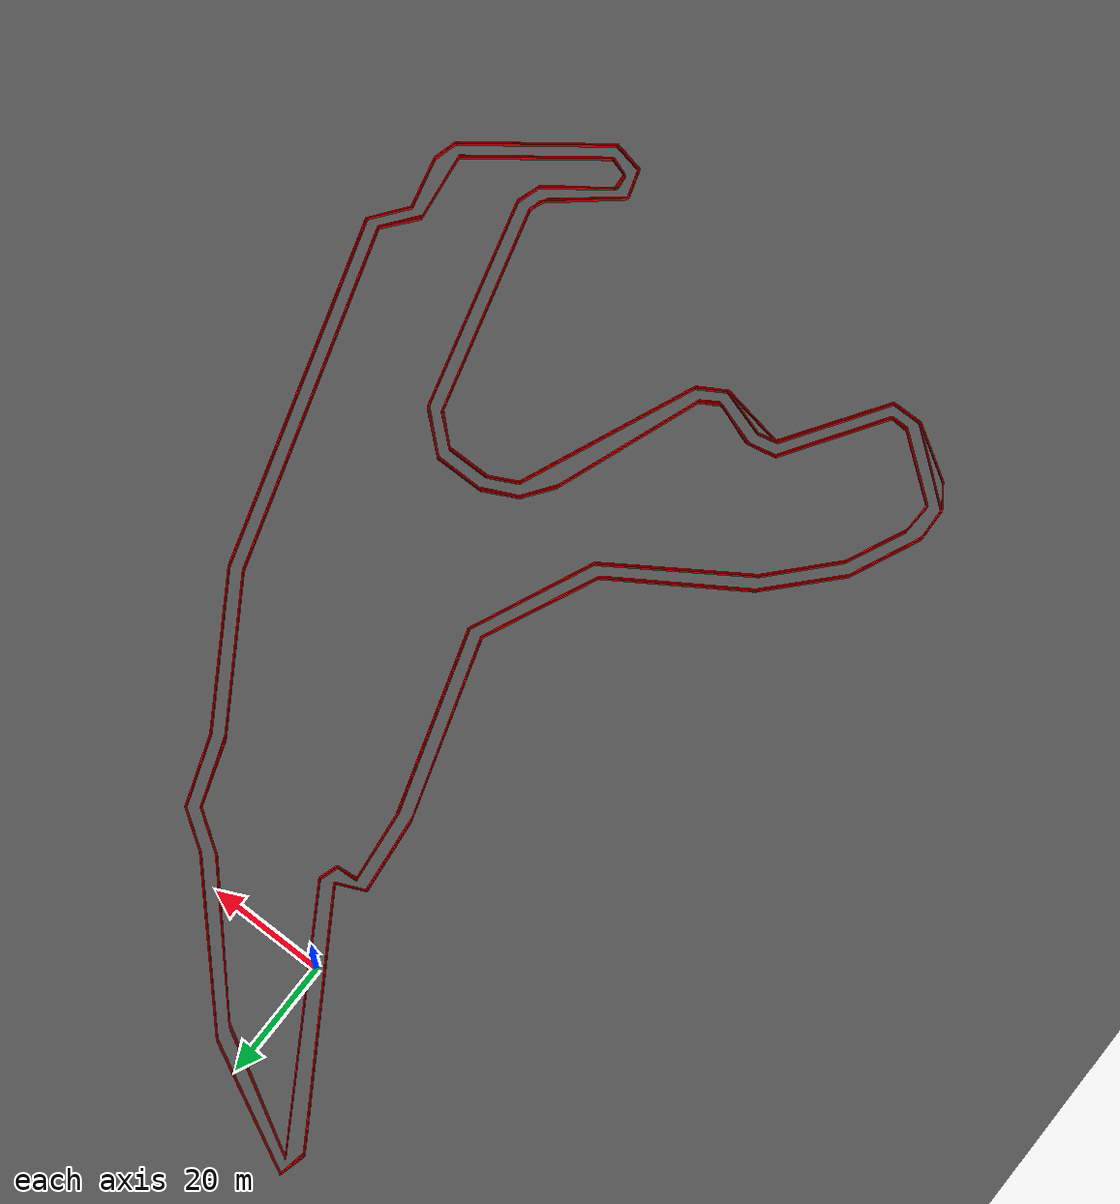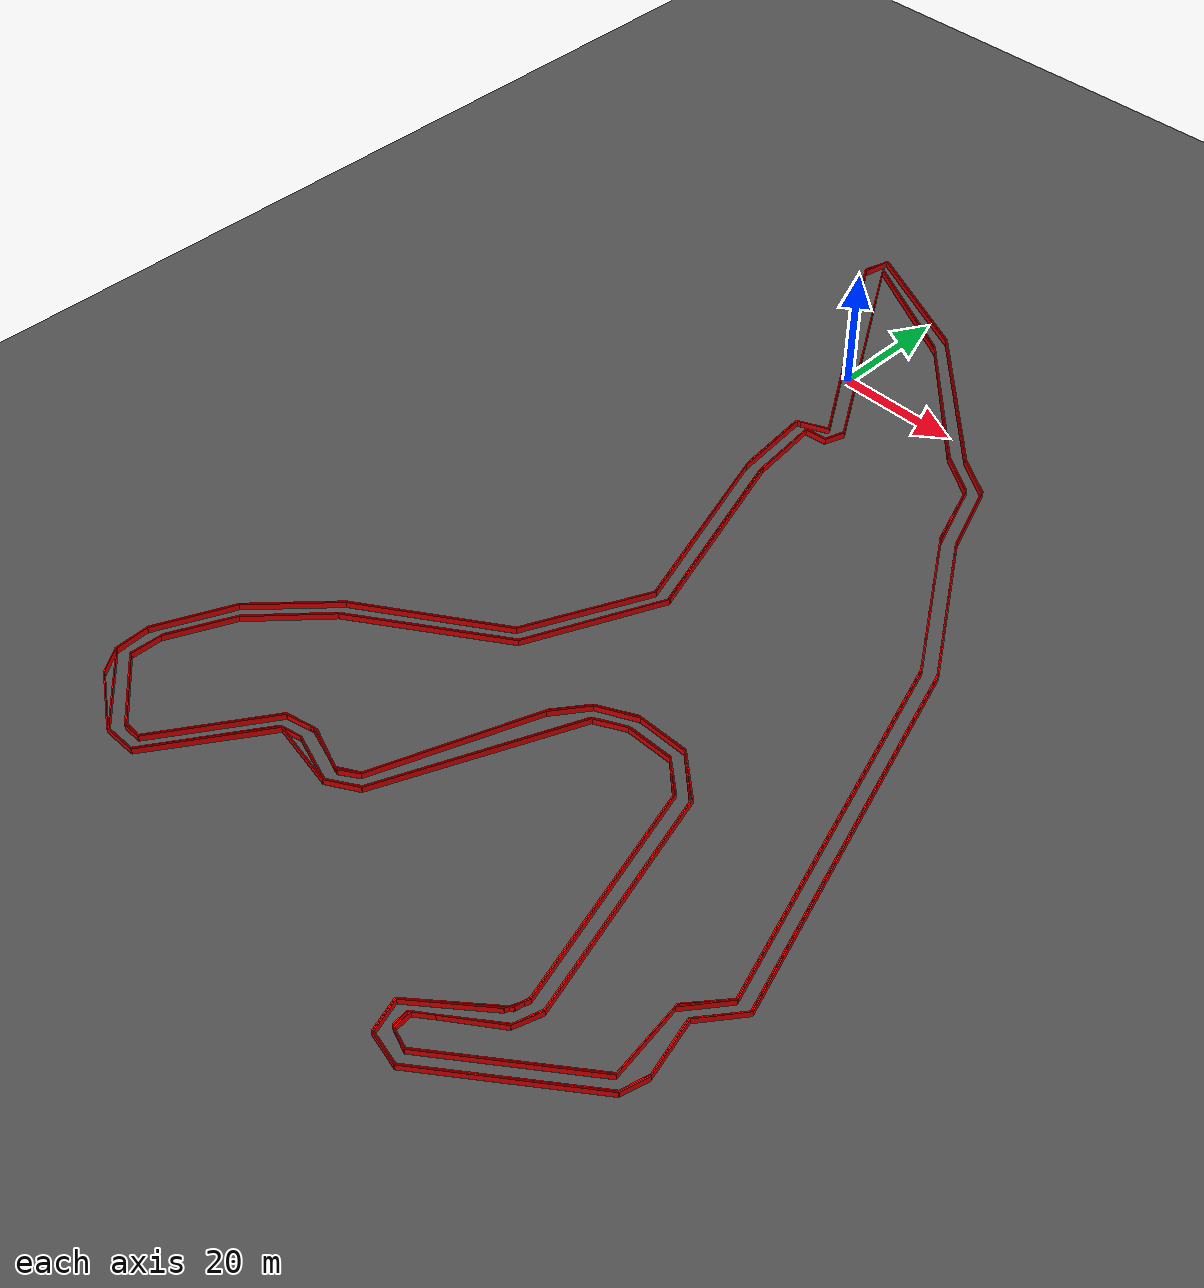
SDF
<?xml version="1.0" ?>
<sdf version="1.6">
  <world name="track_world">
    <scene>
      <ambient>0.4 0.4 0.4 1</ambient>
      <background>0.7 0.7 0.7 1</background>
      <shadows>true</shadows>
    </scene>
    <light name="sun" type="directional">
      <pose>0 0 10 0 0 0</pose>
      <diffuse>0.8 0.8 0.8 1</diffuse>
      <direction>-0.5 0.1 -0.9</direction>
    </light>
    <model name="ground_plane">
      <static>true</static>
      <link name="link">
        <collision name="collision">
          <geometry>
            <plane>
              <normal>0 0 1</normal>
              <size>1000 1000</size>
            </plane>
          </geometry>
        </collision>
        <visual name="visual">
          <geometry>
            <plane>
              <normal>0 0 1</normal>
              <size>1000 1000</size>
            </plane>
          </geometry>
          <material>
            <ambient>0.3 0.3 0.3 1</ambient>
            <diffuse>0.3 0.3 0.3 1</diffuse>
          </material>
        </visual>
      </link>
    </model>
    <model name="wall_0">
      <static>true</static>
      <pose>-15.992041944629321 26.23693316114425 0.5 0 0 -1.8352847093441302</pose>
      <link name="link">
        <visual name="visual">
          <geometry>
            <box>
              <size>4.608411176284081 0.15 1.0</size>
            </box>
          </geometry>
          <material>
            <ambient>1 0 0 1</ambient>
            <diffuse>1 0 0 1</diffuse>
          </material>
        </visual>
        <collision name="collision">
          <geometry>
            <box>
              <size>4.608411176284081 0.15 1.0</size>
            </box>
          </geometry>
        </collision>
      </link>
    </model>
    <model name="wall_1">
      <static>true</static>
      <pose>-5.195986944629318 5.942203161144249 0.5 0 0 -1.0080591040338132</pose>
      <link name="link">
        <visual name="visual">
          <geometry>
            <box>
              <size>42.730417360498606 0.15 1.0</size>
            </box>
          </geometry>
          <material>
            <ambient>1 0 0 1</ambient>
            <diffuse>1 0 0 1</diffuse>
          </material>
        </visual>
        <collision name="collision">
          <geometry>
            <box>
              <size>42.730417360498606 0.15 1.0</size>
            </box>
          </geometry>
        </collision>
      </link>
    </model>
    <model name="wall_2">
      <static>true</static>
      <pose>3.839338055370682 -13.19415183885576 0.5 0 0 -2.717923731712275</pose>
      <link name="link">
        <visual name="visual">
          <geometry>
            <box>
              <size>5.184553158855657 0.15 1.0</size>
            </box>
          </geometry>
          <material>
            <ambient>1 0 0 1</ambient>
            <diffuse>1 0 0 1</diffuse>
          </material>
        </visual>
        <collision name="collision">
          <geometry>
            <box>
              <size>5.184553158855657 0.15 1.0</size>
            </box>
          </geometry>
        </collision>
      </link>
    </model>
    <model name="wall_3">
      <static>true</static>
      <pose>2.171278055370678 -20.561416838855763 0.5 0 0 -1.4609462079477658</pose>
      <link name="link">
        <visual name="visual">
          <geometry>
            <box>
              <size>12.679545446777647 0.15 1.0</size>
            </box>
          </geometry>
          <material>
            <ambient>1 0 0 1</ambient>
            <diffuse>1 0 0 1</diffuse>
          </material>
        </visual>
        <collision name="collision">
          <geometry>
            <box>
              <size>12.679545446777647 0.15 1.0</size>
            </box>
          </geometry>
        </collision>
      </link>
    </model>
    <model name="wall_4">
      <static>true</static>
      <pose>7.638808055370681 -42.01452183885576 0.5 0 0 -1.2656494125130227</pose>
      <link name="link">
        <visual name="visual">
          <geometry>
            <box>
              <size>31.770811753057238 0.15 1.0</size>
            </box>
          </geometry>
          <material>
            <ambient>1 0 0 1</ambient>
            <diffuse>1 0 0 1</diffuse>
          </material>
        </visual>
        <collision name="collision">
          <geometry>
            <box>
              <size>31.770811753057238 0.15 1.0</size>
            </box>
          </geometry>
        </collision>
      </link>
    </model>
    <model name="wall_5">
      <static>true</static>
      <pose>8.10215805537068 -66.61840683885575 0.5 0 0 -1.9985312391811392</pose>
      <link name="link">
        <visual name="visual">
          <geometry>
            <box>
              <size>20.776481731960782 0.15 1.0</size>
            </box>
          </geometry>
          <material>
            <ambient>1 0 0 1</ambient>
            <diffuse>1 0 0 1</diffuse>
          </material>
        </visual>
        <collision name="collision">
          <geometry>
            <box>
              <size>20.776481731960782 0.15 1.0</size>
            </box>
          </geometry>
        </collision>
      </link>
    </model>
    <model name="wall_6">
      <static>true</static>
      <pose>-6.632371944629323 -82.83565683885575 0.5 0 0 -2.565998927056457</pose>
      <link name="link">
        <visual name="visual">
          <geometry>
            <box>
              <size>24.855780108355088 0.15 1.0</size>
            </box>
          </geometry>
          <material>
            <ambient>1 0 0 1</ambient>
            <diffuse>1 0 0 1</diffuse>
          </material>
        </visual>
        <collision name="collision">
          <geometry>
            <box>
              <size>24.855780108355088 0.15 1.0</size>
            </box>
          </geometry>
        </collision>
      </link>
    </model>
    <model name="wall_7">
      <static>true</static>
      <pose>-22.154596944629322 -95.06809683885577 0.5 0 0 -2.32112115965912</pose>
      <link name="link">
        <visual name="visual">
          <geometry>
            <box>
              <size>14.949483499224977 0.15 1.0</size>
            </box>
          </geometry>
          <material>
            <ambient>1 0 0 1</ambient>
            <diffuse>1 0 0 1</diffuse>
          </material>
        </visual>
        <collision name="collision">
          <geometry>
            <box>
              <size>14.949483499224977 0.15 1.0</size>
            </box>
          </geometry>
        </collision>
      </link>
    </model>
    <model name="wall_8">
      <static>true</static>
      <pose>-29.93887694462932 -106.46650683885576 0.5 0 0 -1.9962459641649386</pose>
      <link name="link">
        <visual name="visual">
          <geometry>
            <box>
              <size>13.022690594389474 0.15 1.0</size>
            </box>
          </geometry>
          <material>
            <ambient>1 0 0 1</ambient>
            <diffuse>1 0 0 1</diffuse>
          </material>
        </visual>
        <collision name="collision">
          <geometry>
            <box>
              <size>13.022690594389474 0.15 1.0</size>
            </box>
          </geometry>
        </collision>
      </link>
    </model>
    <model name="wall_9">
      <static>true</static>
      <pose>-32.53363694462932 -115.27015683885577 0.5 0 0 -1.5385494443596432</pose>
      <link name="link">
        <visual name="visual">
          <geometry>
            <box>
              <size>5.7485285775753 0.15 1.0</size>
            </box>
          </geometry>
          <material>
            <ambient>1 0 0 1</ambient>
            <diffuse>1 0 0 1</diffuse>
          </material>
        </visual>
        <collision name="collision">
          <geometry>
            <box>
              <size>5.7485285775753 0.15 1.0</size>
            </box>
          </geometry>
        </collision>
      </link>
    </model>
    <model name="wall_10">
      <static>true</static>
      <pose>-31.09725194462932 -120.08899683885576 0.5 0 0 -0.9664908199286656</pose>
      <link name="link">
        <visual name="visual">
          <geometry>
            <box>
              <size>4.729802721520213 0.15 1.0</size>
            </box>
          </geometry>
          <material>
            <ambient>1 0 0 1</ambient>
            <diffuse>1 0 0 1</diffuse>
          </material>
        </visual>
        <collision name="collision">
          <geometry>
            <box>
              <size>4.729802721520213 0.15 1.0</size>
            </box>
          </geometry>
        </collision>
      </link>
    </model>
    <model name="wall_11">
      <static>true</static>
      <pose>-25.398046944629318 -124.90783683885576 0.5 0 0 -0.583076535019145</pose>
      <link name="link">
        <visual name="visual">
          <geometry>
            <box>
              <size>10.435152248625798 0.15 1.0</size>
            </box>
          </geometry>
          <material>
            <ambient>1 0 0 1</ambient>
            <diffuse>1 0 0 1</diffuse>
          </material>
        </visual>
        <collision name="collision">
          <geometry>
            <box>
              <size>10.435152248625798 0.15 1.0</size>
            </box>
          </geometry>
        </collision>
      </link>
    </model>
    <model name="wall_12">
      <static>true</static>
      <pose>-18.35512694462932 -127.78060683885576 0.5 0 0 0.0</pose>
      <link name="link">
        <visual name="visual">
          <geometry>
            <box>
              <size>5.374859999999998 0.15 1.0</size>
            </box>
          </geometry>
          <material>
            <ambient>1 0 0 1</ambient>
            <diffuse>1 0 0 1</diffuse>
          </material>
        </visual>
        <collision name="collision">
          <geometry>
            <box>
              <size>5.374859999999998 0.15 1.0</size>
            </box>
          </geometry>
        </collision>
      </link>
    </model>
    <model name="wall_13">
      <static>true</static>
      <pose>-10.15383194462932 -119.48664183885576 0.5 0 0 0.9840840451118751</pose>
      <link name="link">
        <visual name="visual">
          <geometry>
            <box>
              <size>19.919092615824646 0.15 1.0</size>
            </box>
          </geometry>
          <material>
            <ambient>1 0 0 1</ambient>
            <diffuse>1 0 0 1</diffuse>
          </material>
        </visual>
        <collision name="collision">
          <geometry>
            <box>
              <size>19.919092615824646 0.15 1.0</size>
            </box>
          </geometry>
        </collision>
      </link>
    </model>
    <model name="wall_14">
      <static>true</static>
      <pose>0.8275630553706819 -112.21204683885576 0.5 0 0 -0.184324408899698</pose>
      <link name="link">
        <visual name="visual">
          <geometry>
            <box>
              <size>11.12348857109136 0.15 1.0</size>
            </box>
          </geometry>
          <material>
            <ambient>1 0 0 1</ambient>
            <diffuse>1 0 0 1</diffuse>
          </material>
        </visual>
        <collision name="collision">
          <geometry>
            <box>
              <size>11.12348857109136 0.15 1.0</size>
            </box>
          </geometry>
        </collision>
      </link>
    </model>
    <model name="wall_15">
      <static>true</static>
      <pose>8.611843055370684 -111.88770183885575 0.5 0 0 0.5255837935516091</pose>
      <link name="link">
        <visual name="visual">
          <geometry>
            <box>
              <size>5.3564542614401125 0.15 1.0</size>
            </box>
          </geometry>
          <material>
            <ambient>1 0 0 1</ambient>
            <diffuse>1 0 0 1</diffuse>
          </material>
        </visual>
        <collision name="collision">
          <geometry>
            <box>
              <size>5.3564542614401125 0.15 1.0</size>
            </box>
          </geometry>
        </collision>
      </link>
    </model>
    <model name="wall_16">
      <static>true</static>
      <pose>17.18381805537068 -95.67045183885577 0.5 0 0 1.1726917666035248</pose>
      <link name="link">
        <visual name="visual">
          <geometry>
            <box>
              <size>32.270722532775736 0.15 1.0</size>
            </box>
          </geometry>
          <material>
            <ambient>1 0 0 1</ambient>
            <diffuse>1 0 0 1</diffuse>
          </material>
        </visual>
        <collision name="collision">
          <geometry>
            <box>
              <size>32.270722532775736 0.15 1.0</size>
            </box>
          </geometry>
        </collision>
      </link>
    </model>
    <model name="wall_17">
      <static>true</static>
      <pose>25.709458055370675 -79.63854183885576 0.5 0 0 0.4717775111807499</pose>
      <link name="link">
        <visual name="visual">
          <geometry>
            <box>
              <size>5.097692384932617 0.15 1.0</size>
            </box>
          </geometry>
          <material>
            <ambient>1 0 0 1</ambient>
            <diffuse>1 0 0 1</diffuse>
          </material>
        </visual>
        <collision name="collision">
          <geometry>
            <box>
              <size>5.097692384932617 0.15 1.0</size>
            </box>
          </geometry>
        </collision>
      </link>
    </model>
    <model name="wall_18">
      <static>true</static>
      <pose>31.82567805537068 -78.48016683885577 0.5 0 0 0.0</pose>
      <link name="link">
        <visual name="visual">
          <geometry>
            <box>
              <size>7.691610000000011 0.15 1.0</size>
            </box>
          </geometry>
          <material>
            <ambient>1 0 0 1</ambient>
            <diffuse>1 0 0 1</diffuse>
          </material>
        </visual>
        <collision name="collision">
          <geometry>
            <box>
              <size>7.691610000000011 0.15 1.0</size>
            </box>
          </geometry>
        </collision>
      </link>
    </model>
    <model name="wall_19">
      <static>true</static>
      <pose>38.034568055370684 -80.65791183885577 0.5 0 0 -0.7446044805295821</pose>
      <link name="link">
        <visual name="visual">
          <geometry>
            <box>
              <size>6.427050335029271 0.15 1.0</size>
            </box>
          </geometry>
          <material>
            <ambient>1 0 0 1</ambient>
            <diffuse>1 0 0 1</diffuse>
          </material>
        </visual>
        <collision name="collision">
          <geometry>
            <box>
              <size>6.427050335029271 0.15 1.0</size>
            </box>
          </geometry>
        </collision>
      </link>
    </model>
    <model name="wall_20">
      <static>true</static>
      <pose>45.26282805537068 -100.30395183885577 0.5 0 0 -1.2991655755919616</pose>
      <link name="link">
        <visual name="visual">
          <geometry>
            <box>
              <size>36.266307117634696 0.15 1.0</size>
            </box>
          </geometry>
          <material>
            <ambient>1 0 0 1</ambient>
            <diffuse>1 0 0 1</diffuse>
          </material>
        </visual>
        <collision name="collision">
          <geometry>
            <box>
              <size>36.266307117634696 0.15 1.0</size>
            </box>
          </geometry>
        </collision>
      </link>
    </model>
    <model name="wall_21">
      <static>true</static>
      <pose>49.94266305537068 -118.88428683885576 0.5 0 0 -1.7359450042095266</pose>
      <link name="link">
        <visual name="visual">
          <geometry>
            <box>
              <size>2.254758414730946 0.15 1.0</size>
            </box>
          </geometry>
          <material>
            <ambient>1 0 0 1</ambient>
            <diffuse>1 0 0 1</diffuse>
          </material>
        </visual>
        <collision name="collision">
          <geometry>
            <box>
              <size>2.254758414730946 0.15 1.0</size>
            </box>
          </geometry>
        </collision>
      </link>
    </model>
    <model name="wall_22">
      <static>true</static>
      <pose>44.28979305537068 -124.58349183885576 0.5 0 0 -2.443529368865176</pose>
      <link name="link">
        <visual name="visual">
          <geometry>
            <box>
              <size>14.273887632754429 0.15 1.0</size>
            </box>
          </geometry>
          <material>
            <ambient>1 0 0 1</ambient>
            <diffuse>1 0 0 1</diffuse>
          </material>
        </visual>
        <collision name="collision">
          <geometry>
            <box>
              <size>14.273887632754429 0.15 1.0</size>
            </box>
          </geometry>
        </collision>
      </link>
    </model>
    <model name="wall_23">
      <static>true</static>
      <pose>39.60995805537068 -131.67274683885574 0.5 0 0 -1.2658039799804917</pose>
      <link name="link">
        <visual name="visual">
          <geometry>
            <box>
              <size>5.2463007085469195 0.15 1.0</size>
            </box>
          </geometry>
          <material>
            <ambient>1 0 0 1</ambient>
            <diffuse>1 0 0 1</diffuse>
          </material>
        </visual>
        <collision name="collision">
          <geometry>
            <box>
              <size>5.2463007085469195 0.15 1.0</size>
            </box>
          </geometry>
        </collision>
      </link>
    </model>
    <model name="wall_24">
      <static>true</static>
      <pose>43.08508305537068 -134.77719183885574 0.5 0 0 -0.22049376136667279</pose>
      <link name="link">
        <visual name="visual">
          <geometry>
            <box>
              <size>5.508216245183189 0.15 1.0</size>
            </box>
          </geometry>
          <material>
            <ambient>1 0 0 1</ambient>
            <diffuse>1 0 0 1</diffuse>
          </material>
        </visual>
        <collision name="collision">
          <geometry>
            <box>
              <size>5.508216245183189 0.15 1.0</size>
            </box>
          </geometry>
        </collision>
      </link>
    </model>
    <model name="wall_25">
      <static>true</static>
      <pose>56.24422305537068 -127.50259683885577 0.5 0 0 0.6449155350070506</pose>
      <link name="link">
        <visual name="visual">
          <geometry>
            <box>
              <size>26.20710221497982 0.15 1.0</size>
            </box>
          </geometry>
          <material>
            <ambient>1 0 0 1</ambient>
            <diffuse>1 0 0 1</diffuse>
          </material>
        </visual>
        <collision name="collision">
          <geometry>
            <box>
              <size>26.20710221497982 0.15 1.0</size>
            </box>
          </geometry>
        </collision>
      </link>
    </model>
    <model name="wall_26">
      <static>true</static>
      <pose>67.27195305537069 -117.54057183885575 0.5 0 0 1.3101939350475535</pose>
      <link name="link">
        <visual name="visual">
          <geometry>
            <box>
              <size>4.315875807307243 0.15 1.0</size>
            </box>
          </geometry>
          <material>
            <ambient>1 0 0 1</ambient>
            <diffuse>1 0 0 1</diffuse>
          </material>
        </visual>
        <collision name="collision">
          <geometry>
            <box>
              <size>4.315875807307243 0.15 1.0</size>
            </box>
          </geometry>
        </collision>
      </link>
    </model>
    <model name="wall_27">
      <static>true</static>
      <pose>66.71593305537068 -110.96100183885576 0.5 0 0 1.8133478102220888</pose>
      <link name="link">
        <visual name="visual">
          <geometry>
            <box>
              <size>9.260047141699662 0.15 1.0</size>
            </box>
          </geometry>
          <material>
            <ambient>1 0 0 1</ambient>
            <diffuse>1 0 0 1</diffuse>
          </material>
        </visual>
        <collision name="collision">
          <geometry>
            <box>
              <size>9.260047141699662 0.15 1.0</size>
            </box>
          </geometry>
        </collision>
      </link>
    </model>
    <model name="wall_28">
      <static>true</static>
      <pose>67.87430805537068 -103.45473183885576 0.5 0 0 0.9248382204887861</pose>
      <link name="link">
        <visual name="visual">
          <geometry>
            <box>
              <size>7.543360769007406 0.15 1.0</size>
            </box>
          </geometry>
          <material>
            <ambient>1 0 0 1</ambient>
            <diffuse>1 0 0 1</diffuse>
          </material>
        </visual>
        <collision name="collision">
          <geometry>
            <box>
              <size>7.543360769007406 0.15 1.0</size>
            </box>
          </geometry>
        </collision>
      </link>
    </model>
    <model name="wall_29">
      <static>true</static>
      <pose>60.69238305537068 -71.06656683885576 0.5 0 0 1.8821009173765633</pose>
      <link name="link">
        <visual name="visual">
          <geometry>
            <box>
              <size>61.71933314311489 0.15 1.0</size>
            </box>
          </geometry>
          <material>
            <ambient>1 0 0 1</ambient>
            <diffuse>1 0 0 1</diffuse>
          </material>
        </visual>
        <collision name="collision">
          <geometry>
            <box>
              <size>61.71933314311489 0.15 1.0</size>
            </box>
          </geometry>
        </collision>
      </link>
    </model>
    <model name="wall_30">
      <static>true</static>
      <pose>43.82644305537068 -30.199096838855766 0.5 0 0 2.143762469683603</pose>
      <link name="link">
        <visual name="visual">
          <geometry>
            <box>
              <size>27.350055541179426 0.15 1.0</size>
            </box>
          </geometry>
          <material>
            <ambient>1 0 0 1</ambient>
            <diffuse>1 0 0 1</diffuse>
          </material>
        </visual>
        <collision name="collision">
          <geometry>
            <box>
              <size>27.350055541179426 0.15 1.0</size>
            </box>
          </geometry>
        </collision>
      </link>
    </model>
    <model name="wall_31">
      <static>true</static>
      <pose>34.281433055370684 -12.962476838855764 0.5 0 0 1.9260271888415783</pose>
      <link name="link">
        <visual name="visual">
          <geometry>
            <box>
              <size>12.256286302090054 0.15 1.0</size>
            </box>
          </geometry>
          <material>
            <ambient>1 0 0 1</ambient>
            <diffuse>1 0 0 1</diffuse>
          </material>
        </visual>
        <collision name="collision">
          <geometry>
            <box>
              <size>12.256286302090054 0.15 1.0</size>
            </box>
          </geometry>
        </collision>
      </link>
    </model>
    <model name="wall_32">
      <static>true</static>
      <pose>28.999243055370684 -5.131861838855755 0.5 0 0 2.556991397469466</pose>
      <link name="link">
        <visual name="visual">
          <geometry>
            <box>
              <size>7.556441586891279 0.15 1.0</size>
            </box>
          </geometry>
          <material>
            <ambient>1 0 0 1</ambient>
            <diffuse>1 0 0 1</diffuse>
          </material>
        </visual>
        <collision name="collision">
          <geometry>
            <box>
              <size>7.556441586891279 0.15 1.0</size>
            </box>
          </geometry>
        </collision>
      </link>
    </model>
    <model name="wall_33">
      <static>true</static>
      <pose>15.515758055370682 7.656598161144245 0.5 0 0 2.3385751682947196</pose>
      <link name="link">
        <visual name="visual">
          <geometry>
            <box>
              <size>29.75414210326018 0.15 1.0</size>
            </box>
          </geometry>
          <material>
            <ambient>1 0 0 1</ambient>
            <diffuse>1 0 0 1</diffuse>
          </material>
        </visual>
        <collision name="collision">
          <geometry>
            <box>
              <size>29.75414210326018 0.15 1.0</size>
            </box>
          </geometry>
        </collision>
      </link>
    </model>
    <model name="wall_34">
      <static>true</static>
      <pose>-5.10331694462932 23.410498161144247 0.5 0 0 2.685178191500146</pose>
      <link name="link">
        <visual name="visual">
          <geometry>
            <box>
              <size>22.918735527260225 0.15 1.0</size>
            </box>
          </geometry>
          <material>
            <ambient>1 0 0 1</ambient>
            <diffuse>1 0 0 1</diffuse>
          </material>
        </visual>
        <collision name="collision">
          <geometry>
            <box>
              <size>22.918735527260225 0.15 1.0</size>
            </box>
          </geometry>
        </collision>
      </link>
    </model>
    <model name="wall_35">
      <static>true</static>
      <pose>-5.010646944629322 23.132488161144252 0.5 0 0 -0.4600698067356663</pose>
      <link name="link">
        <visual name="visual">
          <geometry>
            <box>
              <size>23.166943973327594 0.15 1.0</size>
            </box>
          </geometry>
          <material>
            <ambient>1 0 0 1</ambient>
            <diffuse>1 0 0 1</diffuse>
          </material>
        </visual>
        <collision name="collision">
          <geometry>
            <box>
              <size>23.166943973327594 0.15 1.0</size>
            </box>
          </geometry>
        </collision>
      </link>
    </model>
    <model name="wall_36">
      <static>true</static>
      <pose>15.515758055370675 7.42492316114425 0.5 0 0 -0.8055296715278508</pose>
      <link name="link">
        <visual name="visual">
          <geometry>
            <box>
              <size>29.296767140940656 0.15 1.0</size>
            </box>
          </geometry>
          <material>
            <ambient>1 0 0 1</ambient>
            <diffuse>1 0 0 1</diffuse>
          </material>
        </visual>
        <collision name="collision">
          <geometry>
            <box>
              <size>29.296767140940656 0.15 1.0</size>
            </box>
          </geometry>
        </collision>
      </link>
    </model>
    <model name="wall_37">
      <static>true</static>
      <pose>28.86023805537068 -5.270866838855753 0.5 0 0 -0.5880026035475675</pose>
      <link name="link">
        <visual name="visual">
          <geometry>
            <box>
              <size>7.68490804403671 0.15 1.0</size>
            </box>
          </geometry>
          <material>
            <ambient>1 0 0 1</ambient>
            <diffuse>1 0 0 1</diffuse>
          </material>
        </visual>
        <collision name="collision">
          <geometry>
            <box>
              <size>7.68490804403671 0.15 1.0</size>
            </box>
          </geometry>
        </collision>
      </link>
    </model>
    <model name="wall_38">
      <static>true</static>
      <pose>34.188763055370686 -13.14781683885576 0.5 0 0 -1.2155654647482148</pose>
      <link name="link">
        <visual name="visual">
          <geometry>
            <box>
              <size>12.256286302090054 0.15 1.0</size>
            </box>
          </geometry>
          <material>
            <ambient>1 0 0 1</ambient>
            <diffuse>1 0 0 1</diffuse>
          </material>
        </visual>
        <collision name="collision">
          <geometry>
            <box>
              <size>12.256286302090054 0.15 1.0</size>
            </box>
          </geometry>
        </collision>
      </link>
    </model>
    <model name="wall_39">
      <static>true</static>
      <pose>43.687438055370684 -30.291766838855764 0.5 0 0 -0.9969973134713415</pose>
      <link name="link">
        <visual name="visual">
          <geometry>
            <box>
              <size>27.14408547793238 0.15 1.0</size>
            </box>
          </geometry>
          <material>
            <ambient>1 0 0 1</ambient>
            <diffuse>1 0 0 1</diffuse>
          </material>
        </visual>
        <collision name="collision">
          <geometry>
            <box>
              <size>27.14408547793238 0.15 1.0</size>
            </box>
          </geometry>
        </collision>
      </link>
    </model>
    <model name="wall_40">
      <static>true</static>
      <pose>60.50704305537068 -71.15923683885576 0.5 0 0 -1.2604089196625452</pose>
      <link name="link">
        <visual name="visual">
          <geometry>
            <box>
              <size>61.89579076994493 0.15 1.0</size>
            </box>
          </geometry>
          <material>
            <ambient>1 0 0 1</ambient>
            <diffuse>1 0 0 1</diffuse>
          </material>
        </visual>
        <collision name="collision">
          <geometry>
            <box>
              <size>61.89579076994493 0.15 1.0</size>
            </box>
          </geometry>
        </collision>
      </link>
    </model>
    <model name="wall_41">
      <static>true</static>
      <pose>67.68896805537068 -103.59373683885576 0.5 0 0 -2.2242226679756585</pose>
      <link name="link">
        <visual name="visual">
          <geometry>
            <box>
              <size>7.4695699115344 0.15 1.0</size>
            </box>
          </geometry>
          <material>
            <ambient>1 0 0 1</ambient>
            <diffuse>1 0 0 1</diffuse>
          </material>
        </visual>
        <collision name="collision">
          <geometry>
            <box>
              <size>7.4695699115344 0.15 1.0</size>
            </box>
          </geometry>
        </collision>
      </link>
    </model>
    <model name="wall_42">
      <static>true</static>
      <pose>66.53059305537069 -110.91466683885577 0.5 0 0 -1.3208177053340726</pose>
      <link name="link">
        <visual name="visual">
          <geometry>
            <box>
              <size>8.990422927026302 0.15 1.0</size>
            </box>
          </geometry>
          <material>
            <ambient>1 0 0 1</ambient>
            <diffuse>1 0 0 1</diffuse>
          </material>
        </visual>
        <collision name="collision">
          <geometry>
            <box>
              <size>8.990422927026302 0.15 1.0</size>
            </box>
          </geometry>
        </collision>
      </link>
    </model>
    <model name="wall_43">
      <static>true</static>
      <pose>67.13294805537069 -117.35523183885576 0.5 0 0 -1.8105394356653557</pose>
      <link name="link">
        <visual name="visual">
          <geometry>
            <box>
              <size>4.292932123782061 0.15 1.0</size>
            </box>
          </geometry>
          <material>
            <ambient>1 0 0 1</ambient>
            <diffuse>1 0 0 1</diffuse>
          </material>
        </visual>
        <collision name="collision">
          <geometry>
            <box>
              <size>4.292932123782061 0.15 1.0</size>
            </box>
          </geometry>
        </collision>
      </link>
    </model>
    <model name="wall_44">
      <static>true</static>
      <pose>56.19788805537068 -127.31725683885577 0.5 0 0 -2.49454546036947</pose>
      <link name="link">
        <visual name="visual">
          <geometry>
            <box>
              <size>26.133104307994106 0.15 1.0</size>
            </box>
          </geometry>
          <material>
            <ambient>1 0 0 1</ambient>
            <diffuse>1 0 0 1</diffuse>
          </material>
        </visual>
        <collision name="collision">
          <geometry>
            <box>
              <size>26.133104307994106 0.15 1.0</size>
            </box>
          </geometry>
        </collision>
      </link>
    </model>
    <model name="wall_45">
      <static>true</static>
      <pose>43.17775305537068 -134.63818683885575 0.5 0 0 2.9304993203670455</pose>
      <link name="link">
        <visual name="visual">
          <geometry>
            <box>
              <size>5.307329911735281 0.15 1.0</size>
            </box>
          </geometry>
          <material>
            <ambient>1 0 0 1</ambient>
            <diffuse>1 0 0 1</diffuse>
          </material>
        </visual>
        <collision name="collision">
          <geometry>
            <box>
              <size>5.307329911735281 0.15 1.0</size>
            </box>
          </geometry>
        </collision>
      </link>
    </model>
    <model name="wall_46">
      <static>true</static>
      <pose>39.79529805537068 -131.62641183885574 0.5 0 0 1.8811837339272484</pose>
      <link name="link">
        <visual name="visual">
          <geometry>
            <box>
              <size>5.1579825641620705 0.15 1.0</size>
            </box>
          </geometry>
          <material>
            <ambient>1 0 0 1</ambient>
            <diffuse>1 0 0 1</diffuse>
          </material>
        </visual>
        <collision name="collision">
          <geometry>
            <box>
              <size>5.1579825641620705 0.15 1.0</size>
            </box>
          </geometry>
        </collision>
      </link>
    </model>
    <model name="wall_47">
      <static>true</static>
      <pose>44.01178305537068 -125.09317683885575 0.5 0 0 0.6837093116343717</pose>
      <link name="link">
        <visual name="visual">
          <geometry>
            <box>
              <size>12.910098469461802 0.15 1.0</size>
            </box>
          </geometry>
          <material>
            <ambient>1 0 0 1</ambient>
            <diffuse>1 0 0 1</diffuse>
          </material>
        </visual>
        <collision name="collision">
          <geometry>
            <box>
              <size>12.910098469461802 0.15 1.0</size>
            </box>
          </geometry>
        </collision>
      </link>
    </model>
    <model name="wall_48">
      <static>true</static>
      <pose>49.66465305537068 -119.44030683885576 0.5 0 0 1.1801892830972085</pose>
      <link name="link">
        <visual name="visual">
          <geometry>
            <box>
              <size>3.4074344414529816 0.15 1.0</size>
            </box>
          </geometry>
          <material>
            <ambient>1 0 0 1</ambient>
            <diffuse>1 0 0 1</diffuse>
          </material>
        </visual>
        <collision name="collision">
          <geometry>
            <box>
              <size>3.4074344414529816 0.15 1.0</size>
            </box>
          </geometry>
        </collision>
      </link>
    </model>
    <model name="wall_49">
      <static>true</static>
      <pose>45.35549805537068 -100.11861183885577 0.5 0 0 1.8432238598579263</pose>
      <link name="link">
        <visual name="visual">
          <geometry>
            <box>
              <size>36.85167937541246 0.15 1.0</size>
            </box>
          </geometry>
          <material>
            <ambient>1 0 0 1</ambient>
            <diffuse>1 0 0 1</diffuse>
          </material>
        </visual>
        <collision name="collision">
          <geometry>
            <box>
              <size>36.85167937541246 0.15 1.0</size>
            </box>
          </geometry>
        </collision>
      </link>
    </model>
    <model name="wall_50">
      <static>true</static>
      <pose>37.988233055370685 -80.33356683885576 0.5 0 0 2.4393357220807848</pose>
      <link name="link">
        <visual name="visual">
          <geometry>
            <box>
              <size>6.3124529381215995 0.15 1.0</size>
            </box>
          </geometry>
          <material>
            <ambient>1 0 0 1</ambient>
            <diffuse>1 0 0 1</diffuse>
          </material>
        </visual>
        <collision name="collision">
          <geometry>
            <box>
              <size>6.3124529381215995 0.15 1.0</size>
            </box>
          </geometry>
        </collision>
      </link>
    </model>
    <model name="wall_51">
      <static>true</static>
      <pose>31.825678055370688 -78.29482683885576 0.5 0 0 3.141592653589793</pose>
      <link name="link">
        <visual name="visual">
          <geometry>
            <box>
              <size>7.506270000000001 0.15 1.0</size>
            </box>
          </geometry>
          <material>
            <ambient>1 0 0 1</ambient>
            <diffuse>1 0 0 1</diffuse>
          </material>
        </visual>
        <collision name="collision">
          <geometry>
            <box>
              <size>7.506270000000001 0.15 1.0</size>
            </box>
          </geometry>
        </collision>
      </link>
    </model>
    <model name="wall_52">
      <static>true</static>
      <pose>25.663123055370683 -79.49953683885576 0.5 0 0 -2.677945044588986</pose>
      <link name="link">
        <visual name="visual">
          <geometry>
            <box>
              <size>5.387626906347556 0.15 1.0</size>
            </box>
          </geometry>
          <material>
            <ambient>1 0 0 1</ambient>
            <diffuse>1 0 0 1</diffuse>
          </material>
        </visual>
        <collision name="collision">
          <geometry>
            <box>
              <size>5.387626906347556 0.15 1.0</size>
            </box>
          </geometry>
        </collision>
      </link>
    </model>
    <model name="wall_53">
      <static>true</static>
      <pose>17.044813055370682 -95.53144683885577 0.5 0 0 -1.9673612805543843</pose>
      <link name="link">
        <visual name="visual">
          <geometry>
            <box>
              <size>32.14941211730628 0.15 1.0</size>
            </box>
          </geometry>
          <material>
            <ambient>1 0 0 1</ambient>
            <diffuse>1 0 0 1</diffuse>
          </material>
        </visual>
        <collision name="collision">
          <geometry>
            <box>
              <size>32.14941211730628 0.15 1.0</size>
            </box>
          </geometry>
        </collision>
      </link>
    </model>
    <model name="wall_54">
      <static>true</static>
      <pose>8.611843055370684 -111.70236183885575 0.5 0 0 -2.5981150588767514</pose>
      <link name="link">
        <visual name="visual">
          <geometry>
            <box>
              <size>5.196961361266791 0.15 1.0</size>
            </box>
          </geometry>
          <material>
            <ambient>1 0 0 1</ambient>
            <diffuse>1 0 0 1</diffuse>
          </material>
        </visual>
        <collision name="collision">
          <geometry>
            <box>
              <size>5.196961361266791 0.15 1.0</size>
            </box>
          </geometry>
        </collision>
      </link>
    </model>
    <model name="wall_55">
      <static>true</static>
      <pose>2.4029530553706806 -111.74869683885575 0.5 0 0 2.8268349921984854</pose>
      <link name="link">
        <visual name="visual">
          <geometry>
            <box>
              <size>8.381385470314564 0.15 1.0</size>
            </box>
          </geometry>
          <material>
            <ambient>1 0 0 1</ambient>
            <diffuse>1 0 0 1</diffuse>
          </material>
        </visual>
        <collision name="collision">
          <geometry>
            <box>
              <size>8.381385470314564 0.15 1.0</size>
            </box>
          </geometry>
        </collision>
      </link>
    </model>
    <model name="wall_56">
      <static>true</static>
      <pose>-3.2962519446293186 -110.82199683885577 0.5 0 0 -2.9286543040103954</pose>
      <link name="link">
        <visual name="visual">
          <geometry>
            <box>
              <size>3.5080215953867713 0.15 1.0</size>
            </box>
          </geometry>
          <material>
            <ambient>1 0 0 1</ambient>
            <diffuse>1 0 0 1</diffuse>
          </material>
        </visual>
        <collision name="collision">
          <geometry>
            <box>
              <size>3.5080215953867713 0.15 1.0</size>
            </box>
          </geometry>
        </collision>
      </link>
    </model>
    <model name="wall_57">
      <static>true</static>
      <pose>-10.43184194462932 -119.44030683885576 0.5 0 0 -2.152288605655935</pose>
      <link name="link">
        <visual name="visual">
          <geometry>
            <box>
              <size>19.73958012166673 0.15 1.0</size>
            </box>
          </geometry>
          <material>
            <ambient>1 0 0 1</ambient>
            <diffuse>1 0 0 1</diffuse>
          </material>
        </visual>
        <collision name="collision">
          <geometry>
            <box>
              <size>19.73958012166673 0.15 1.0</size>
            </box>
          </geometry>
        </collision>
      </link>
    </model>
    <model name="wall_58">
      <static>true</static>
      <pose>-18.355126944629323 -127.68793683885576 0.5 0 0 3.141592653589793</pose>
      <link name="link">
        <visual name="visual">
          <geometry>
            <box>
              <size>5.004179999999998 0.15 1.0</size>
            </box>
          </geometry>
          <material>
            <ambient>1 0 0 1</ambient>
            <diffuse>1 0 0 1</diffuse>
          </material>
        </visual>
        <collision name="collision">
          <geometry>
            <box>
              <size>5.004179999999998 0.15 1.0</size>
            </box>
          </geometry>
        </collision>
      </link>
    </model>
    <model name="wall_59">
      <static>true</static>
      <pose>-26.55642194462932 -122.91543183885577 0.5 0 0 2.444460128177153</pose>
      <link name="link">
        <visual name="visual">
          <geometry>
            <box>
              <size>14.867110224525815 0.15 1.0</size>
            </box>
          </geometry>
          <material>
            <ambient>1 0 0 1</ambient>
            <diffuse>1 0 0 1</diffuse>
          </material>
        </visual>
        <collision name="collision">
          <geometry>
            <box>
              <size>14.867110224525815 0.15 1.0</size>
            </box>
          </geometry>
        </collision>
      </link>
    </model>
    <model name="wall_60">
      <static>true</static>
      <pose>-32.394631944629324 -115.40916183885577 0.5 0 0 1.6216000308531187</pose>
      <link name="link">
        <visual name="visual">
          <geometry>
            <box>
              <size>5.4745934881961755 0.15 1.0</size>
            </box>
          </geometry>
          <material>
            <ambient>1 0 0 1</ambient>
            <diffuse>1 0 0 1</diffuse>
          </material>
        </visual>
        <collision name="collision">
          <geometry>
            <box>
              <size>5.4745934881961755 0.15 1.0</size>
            </box>
          </geometry>
        </collision>
      </link>
    </model>
    <model name="wall_61">
      <static>true</static>
      <pose>-29.846206944629323 -106.69818183885576 0.5 0 0 1.148264773313587</pose>
      <link name="link">
        <visual name="visual">
          <geometry>
            <box>
              <size>13.107155169772732 0.15 1.0</size>
            </box>
          </geometry>
          <material>
            <ambient>1 0 0 1</ambient>
            <diffuse>1 0 0 1</diffuse>
          </material>
        </visual>
        <collision name="collision">
          <geometry>
            <box>
              <size>13.107155169772732 0.15 1.0</size>
            </box>
          </geometry>
        </collision>
      </link>
    </model>
    <model name="wall_62">
      <static>true</static>
      <pose>-22.01559194462932 -95.20710183885576 0.5 0 0 0.82016675525353</pose>
      <link name="link">
        <visual name="visual">
          <geometry>
            <box>
              <size>15.080458770534799 0.15 1.0</size>
            </box>
          </geometry>
          <material>
            <ambient>1 0 0 1</ambient>
            <diffuse>1 0 0 1</diffuse>
          </material>
        </visual>
        <collision name="collision">
          <geometry>
            <box>
              <size>15.080458770534799 0.15 1.0</size>
            </box>
          </geometry>
        </collision>
      </link>
    </model>
    <model name="wall_63">
      <static>true</static>
      <pose>-6.493366944629322 -82.97466183885577 0.5 0 0 0.5744899125342395</pose>
      <link name="link">
        <visual name="visual">
          <geometry>
            <box>
              <size>24.727613823596077 0.15 1.0</size>
            </box>
          </geometry>
          <material>
            <ambient>1 0 0 1</ambient>
            <diffuse>1 0 0 1</diffuse>
          </material>
        </visual>
        <collision name="collision">
          <geometry>
            <box>
              <size>24.727613823596077 0.15 1.0</size>
            </box>
          </geometry>
        </collision>
      </link>
    </model>
    <model name="wall_64">
      <static>true</static>
      <pose>8.241163055370677 -66.66474183885576 0.5 0 0 1.144532867143021</pose>
      <link name="link">
        <visual name="visual">
          <geometry>
            <box>
              <size>21.067908491269378 0.15 1.0</size>
            </box>
          </geometry>
          <material>
            <ambient>1 0 0 1</ambient>
            <diffuse>1 0 0 1</diffuse>
          </material>
        </visual>
        <collision name="collision">
          <geometry>
            <box>
              <size>21.067908491269378 0.15 1.0</size>
            </box>
          </geometry>
        </collision>
      </link>
    </model>
    <model name="wall_65">
      <static>true</static>
      <pose>7.870483055370677 -42.38520183885576 0.5 0 0 1.8821009173765635</pose>
      <link name="link">
        <visual name="visual">
          <geometry>
            <box>
              <size>30.859666571557447 0.15 1.0</size>
            </box>
          </geometry>
          <material>
            <ambient>1 0 0 1</ambient>
            <diffuse>1 0 0 1</diffuse>
          </material>
        </visual>
        <collision name="collision">
          <geometry>
            <box>
              <size>30.859666571557447 0.15 1.0</size>
            </box>
          </geometry>
        </collision>
      </link>
    </model>
    <model name="wall_66">
      <static>true</static>
      <pose>2.4029530553706735 -20.932096838855763 0.5 0 0 1.6799497897037745</pose>
      <link name="link">
        <visual name="visual">
          <geometry>
            <box>
              <size>13.610822452401607 0.15 1.0</size>
            </box>
          </geometry>
          <material>
            <ambient>1 0 0 1</ambient>
            <diffuse>1 0 0 1</diffuse>
          </material>
        </visual>
        <collision name="collision">
          <geometry>
            <box>
              <size>13.610822452401607 0.15 1.0</size>
            </box>
          </geometry>
        </collision>
      </link>
    </model>
    <model name="wall_67">
      <static>true</static>
      <pose>4.0246780553706785 -13.14781683885576 0.5 0 0 0.4072558480748493</pose>
      <link name="link">
        <visual name="visual">
          <geometry>
            <box>
              <size>5.147149080461938 0.15 1.0</size>
            </box>
          </geometry>
          <material>
            <ambient>1 0 0 1</ambient>
            <diffuse>1 0 0 1</diffuse>
          </material>
        </visual>
        <collision name="collision">
          <geometry>
            <box>
              <size>5.147149080461938 0.15 1.0</size>
            </box>
          </geometry>
        </collision>
      </link>
    </model>
    <model name="wall_68">
      <static>true</static>
      <pose>-4.91797694462932 5.803198161144252 0.5 0 0 2.133334454021195</pose>
      <link name="link">
        <visual name="visual">
          <geometry>
            <box>
              <size>42.39639840145034 0.15 1.0</size>
            </box>
          </geometry>
          <material>
            <ambient>1 0 0 1</ambient>
            <diffuse>1 0 0 1</diffuse>
          </material>
        </visual>
        <collision name="collision">
          <geometry>
            <box>
              <size>42.39639840145034 0.15 1.0</size>
            </box>
          </geometry>
        </collision>
      </link>
    </model>
    <model name="wall_69">
      <static>true</static>
      <pose>-15.80670194462932 26.005258161144255 0.5 0 0 1.3891474967948836</pose>
      <link name="link">
        <visual name="visual">
          <geometry>
            <box>
              <size>4.616789266340842 0.15 1.0</size>
            </box>
          </geometry>
          <material>
            <ambient>1 0 0 1</ambient>
            <diffuse>1 0 0 1</diffuse>
          </material>
        </visual>
        <collision name="collision">
          <geometry>
            <box>
              <size>4.616789266340842 0.15 1.0</size>
            </box>
          </geometry>
        </collision>
      </link>
    </model>
    <model name="wall_70">
      <static>true</static>
      <pose>-3.064576944629323 7.471258161144235 0.5 0 0 -1.01914134426635</pose>
      <link name="link">
        <visual name="visual">
          <geometry>
            <box>
              <size>43.85093090443691 0.15 1.0</size>
            </box>
          </geometry>
          <material>
            <ambient>1 0 0 1</ambient>
            <diffuse>1 0 0 1</diffuse>
          </material>
        </visual>
        <collision name="collision">
          <geometry>
            <box>
              <size>43.85093090443691 0.15 1.0</size>
            </box>
          </geometry>
        </collision>
      </link>
    </model>
    <model name="wall_71">
      <static>true</static>
      <pose>7.916818055370676 -12.777136838855768 0.5 0 0 -1.8836975546752799</pose>
      <link name="link">
        <visual name="visual">
          <geometry>
            <box>
              <size>3.311575124514009 0.15 1.0</size>
            </box>
          </geometry>
          <material>
            <ambient>1 0 0 1</ambient>
            <diffuse>1 0 0 1</diffuse>
          </material>
        </visual>
        <collision name="collision">
          <geometry>
            <box>
              <size>3.311575124514009 0.15 1.0</size>
            </box>
          </geometry>
        </collision>
      </link>
    </model>
    <model name="wall_72">
      <static>true</static>
      <pose>5.646403055370676 -14.445196838855765 0.5 0 0 -3.0890095919788525</pose>
      <link name="link">
        <visual name="visual">
          <geometry>
            <box>
              <size>3.5263339954122372 0.15 1.0</size>
            </box>
          </geometry>
          <material>
            <ambient>1 0 0 1</ambient>
            <diffuse>1 0 0 1</diffuse>
          </material>
        </visual>
        <collision name="collision">
          <geometry>
            <box>
              <size>3.5263339954122372 0.15 1.0</size>
            </box>
          </geometry>
        </collision>
      </link>
    </model>
    <model name="wall_73">
      <static>true</static>
      <pose>4.580698055370675 -20.74675683885576 0.5 0 0 -1.459320104985118</pose>
      <link name="link">
        <visual name="visual">
          <geometry>
            <box>
              <size>12.495339096275053 0.15 1.0</size>
            </box>
          </geometry>
          <material>
            <ambient>1 0 0 1</ambient>
            <diffuse>1 0 0 1</diffuse>
          </material>
        </visual>
        <collision name="collision">
          <geometry>
            <box>
              <size>12.495339096275053 0.15 1.0</size>
            </box>
          </geometry>
        </collision>
      </link>
    </model>
    <model name="wall_74">
      <static>true</static>
      <pose>10.048228055370679 -42.01452183885576 0.5 0 0 -1.2638869832095208</pose>
      <link name="link">
        <visual name="visual">
          <geometry>
            <box>
              <size>31.59408300556609 0.15 1.0</size>
            </box>
          </geometry>
          <material>
            <ambient>1 0 0 1</ambient>
            <diffuse>1 0 0 1</diffuse>
          </material>
        </visual>
        <collision name="collision">
          <geometry>
            <box>
              <size>31.59408300556609 0.15 1.0</size>
            </box>
          </geometry>
        </collision>
      </link>
    </model>
    <model name="wall_75">
      <static>true</static>
      <pose>10.279903055370681 -67.26709683885576 0.5 0 0 -1.989863826494717</pose>
      <link name="link">
        <visual name="visual">
          <geometry>
            <box>
              <size>22.318660961527236 0.15 1.0</size>
            </box>
          </geometry>
          <material>
            <ambient>1 0 0 1</ambient>
            <diffuse>1 0 0 1</diffuse>
          </material>
        </visual>
        <collision name="collision">
          <geometry>
            <box>
              <size>22.318660961527236 0.15 1.0</size>
            </box>
          </geometry>
        </collision>
      </link>
    </model>
    <model name="wall_76">
      <static>true</static>
      <pose>-5.149651944629319 -84.64272183885575 0.5 0 0 -2.558516118570649</pose>
      <link name="link">
        <visual name="visual">
          <geometry>
            <box>
              <size>26.08788062156449 0.15 1.0</size>
            </box>
          </geometry>
          <material>
            <ambient>1 0 0 1</ambient>
            <diffuse>1 0 0 1</diffuse>
          </material>
        </visual>
        <collision name="collision">
          <geometry>
            <box>
              <size>26.08788062156449 0.15 1.0</size>
            </box>
          </geometry>
        </collision>
      </link>
    </model>
    <model name="wall_77">
      <static>true</static>
      <pose>-20.71821194462932 -96.92149683885576 0.5 0 0 -2.3135663013202583</pose>
      <link name="link">
        <visual name="visual">
          <geometry>
            <box>
              <size>13.838892376158583 0.15 1.0</size>
            </box>
          </geometry>
          <material>
            <ambient>1 0 0 1</ambient>
            <diffuse>1 0 0 1</diffuse>
          </material>
        </visual>
        <collision name="collision">
          <geometry>
            <box>
              <size>13.838892376158583 0.15 1.0</size>
            </box>
          </geometry>
        </collision>
      </link>
    </model>
    <model name="wall_78">
      <static>true</static>
      <pose>-27.66846194462932 -106.88352183885576 0.5 0 0 -2.0074234866084377</pose>
      <link name="link">
        <visual name="visual">
          <geometry>
            <box>
              <size>10.737730123792458 0.15 1.0</size>
            </box>
          </geometry>
          <material>
            <ambient>1 0 0 1</ambient>
            <diffuse>1 0 0 1</diffuse>
          </material>
        </visual>
        <collision name="collision">
          <geometry>
            <box>
              <size>10.737730123792458 0.15 1.0</size>
            </box>
          </geometry>
        </collision>
      </link>
    </model>
    <model name="wall_79">
      <static>true</static>
      <pose>-30.077881944629322 -114.52879683885575 0.5 0 0 -1.6207547225168397</pose>
      <link name="link">
        <visual name="visual">
          <geometry>
            <box>
              <size>5.5671459115151585 0.15 1.0</size>
            </box>
          </geometry>
          <material>
            <ambient>1 0 0 1</ambient>
            <diffuse>1 0 0 1</diffuse>
          </material>
        </visual>
        <collision name="collision">
          <geometry>
            <box>
              <size>5.5671459115151585 0.15 1.0</size>
            </box>
          </geometry>
        </collision>
      </link>
    </model>
    <model name="wall_80">
      <static>true</static>
      <pose>-25.02736694462932 -121.52538183885576 0.5 0 0 -0.6823165548747477</pose>
      <link name="link">
        <visual name="visual">
          <geometry>
            <box>
              <size>13.373086941409602 0.15 1.0</size>
            </box>
          </geometry>
          <material>
            <ambient>1 0 0 1</ambient>
            <diffuse>1 0 0 1</diffuse>
          </material>
        </visual>
        <collision name="collision">
          <geometry>
            <box>
              <size>13.373086941409602 0.15 1.0</size>
            </box>
          </geometry>
        </collision>
      </link>
    </model>
    <model name="wall_81">
      <static>true</static>
      <pose>-18.35512694462932 -125.74186683885576 0.5 0 0 0.0</pose>
      <link name="link">
        <visual name="visual">
          <geometry>
            <box>
              <size>2.965440000000001 0.15 1.0</size>
            </box>
          </geometry>
          <material>
            <ambient>1 0 0 1</ambient>
            <diffuse>1 0 0 1</diffuse>
          </material>
        </visual>
        <collision name="collision">
          <geometry>
            <box>
              <size>2.965440000000001 0.15 1.0</size>
            </box>
          </geometry>
        </collision>
      </link>
    </model>
    <model name="wall_82">
      <static>true</static>
      <pose>-11.451211944629321 -117.49423683885576 0.5 0 0 0.9893040479338583</pose>
      <link name="link">
        <visual name="visual">
          <geometry>
            <box>
              <size>19.73958012166671 0.15 1.0</size>
            </box>
          </geometry>
          <material>
            <ambient>1 0 0 1</ambient>
            <diffuse>1 0 0 1</diffuse>
          </material>
        </visual>
        <collision name="collision">
          <geometry>
            <box>
              <size>19.73958012166671 0.15 1.0</size>
            </box>
          </geometry>
        </collision>
      </link>
    </model>
    <model name="wall_83">
      <static>true</static>
      <pose>-3.805936944629323 -108.73692183885576 0.5 0 0 0.22527677921405717</pose>
      <link name="link">
        <visual name="visual">
          <geometry>
            <box>
              <size>4.563468262462228 0.15 1.0</size>
            </box>
          </geometry>
          <material>
            <ambient>1 0 0 1</ambient>
            <diffuse>1 0 0 1</diffuse>
          </material>
        </visual>
        <collision name="collision">
          <geometry>
            <box>
              <size>4.563468262462228 0.15 1.0</size>
            </box>
          </geometry>
        </collision>
      </link>
    </model>
    <model name="wall_84">
      <static>true</static>
      <pose>2.3566180553706815 -109.52461683885576 0.5 0 0 -0.3182170001987814</pose>
      <link name="link">
        <visual name="visual">
          <geometry>
            <box>
              <size>8.293317837880094 0.15 1.0</size>
            </box>
          </geometry>
          <material>
            <ambient>1 0 0 1</ambient>
            <diffuse>1 0 0 1</diffuse>
          </material>
        </visual>
        <collision name="collision">
          <geometry>
            <box>
              <size>8.293317837880094 0.15 1.0</size>
            </box>
          </geometry>
        </collision>
      </link>
    </model>
    <model name="wall_85">
      <static>true</static>
      <pose>7.6851430553706805 -109.94163183885576 0.5 0 0 0.564569393668104</pose>
      <link name="link">
        <visual name="visual">
          <geometry>
            <box>
              <size>3.290763762852019 0.15 1.0</size>
            </box>
          </geometry>
          <material>
            <ambient>1 0 0 1</ambient>
            <diffuse>1 0 0 1</diffuse>
          </material>
        </visual>
        <collision name="collision">
          <geometry>
            <box>
              <size>3.290763762852019 0.15 1.0</size>
            </box>
          </geometry>
        </collision>
      </link>
    </model>
    <model name="wall_86">
      <static>true</static>
      <pose>13.616023055370675 -96.64348683885575 0.5 0 0 1.2202289179577397</pose>
      <link name="link">
        <visual name="visual">
          <geometry>
            <box>
              <size>26.443932931188584 0.15 1.0</size>
            </box>
          </geometry>
          <material>
            <ambient>1 0 0 1</ambient>
            <diffuse>1 0 0 1</diffuse>
          </material>
        </visual>
        <collision name="collision">
          <geometry>
            <box>
              <size>26.443932931188584 0.15 1.0</size>
            </box>
          </geometry>
        </collision>
      </link>
    </model>
    <model name="wall_87">
      <static>true</static>
      <pose>20.056588055370675 -81.58461183885575 0.5 0 0 0.9472355946358713</pose>
      <link name="link">
        <visual name="visual">
          <geometry>
            <box>
              <size>6.506727555153973 0.15 1.0</size>
            </box>
          </geometry>
          <material>
            <ambient>1 0 0 1</ambient>
            <diffuse>1 0 0 1</diffuse>
          </material>
        </visual>
        <collision name="collision">
          <geometry>
            <box>
              <size>6.506727555153973 0.15 1.0</size>
            </box>
          </geometry>
        </collision>
      </link>
    </model>
    <model name="wall_88">
      <static>true</static>
      <pose>24.968098055370675 -77.50713183885576 0.5 0 0 0.4450162247555417</pose>
      <link name="link">
        <visual name="visual">
          <geometry>
            <box>
              <size>6.673526959217294 0.15 1.0</size>
            </box>
          </geometry>
          <material>
            <ambient>1 0 0 1</ambient>
            <diffuse>1 0 0 1</diffuse>
          </material>
        </visual>
        <collision name="collision">
          <geometry>
            <box>
              <size>6.673526959217294 0.15 1.0</size>
            </box>
          </geometry>
        </collision>
      </link>
    </model>
    <model name="wall_89">
      <static>true</static>
      <pose>32.057353055370676 -76.11708183885577 0.5 0 0 -0.011363147264292252</pose>
      <link name="link">
        <visual name="visual">
          <geometry>
            <box>
              <size>8.155486517093879 0.15 1.0</size>
            </box>
          </geometry>
          <material>
            <ambient>1 0 0 1</ambient>
            <diffuse>1 0 0 1</diffuse>
          </material>
        </visual>
        <collision name="collision">
          <geometry>
            <box>
              <size>8.155486517093879 0.15 1.0</size>
            </box>
          </geometry>
        </collision>
      </link>
    </model>
    <model name="wall_90">
      <static>true</static>
      <pose>39.37828305537068 -79.08252183885577 0.5 0 0 -0.7328151017865052</pose>
      <link name="link">
        <visual name="visual">
          <geometry>
            <box>
              <size>8.727231383096242 0.15 1.0</size>
            </box>
          </geometry>
          <material>
            <ambient>1 0 0 1</ambient>
            <diffuse>1 0 0 1</diffuse>
          </material>
        </visual>
        <collision name="collision">
          <geometry>
            <box>
              <size>8.727231383096242 0.15 1.0</size>
            </box>
          </geometry>
        </collision>
      </link>
    </model>
    <model name="wall_91">
      <static>true</static>
      <pose>47.57957805537069 -99.88693683885576 0.5 0 0 -1.300384021374158</pose>
      <link name="link">
        <visual name="visual">
          <geometry>
            <box>
              <size>37.11951189550451 0.15 1.0</size>
            </box>
          </geometry>
          <material>
            <ambient>1 0 0 1</ambient>
            <diffuse>1 0 0 1</diffuse>
          </material>
        </visual>
        <collision name="collision">
          <geometry>
            <box>
              <size>37.11951189550451 0.15 1.0</size>
            </box>
          </geometry>
        </collision>
      </link>
    </model>
    <model name="wall_92">
      <static>true</static>
      <pose>51.935068055370685 -119.81098683885577 0.5 0 0 -1.8580777801920356</pose>
      <link name="link">
        <visual name="visual">
          <geometry>
            <box>
              <size>4.25172545380108 0.15 1.0</size>
            </box>
          </geometry>
          <material>
            <ambient>1 0 0 1</ambient>
            <diffuse>1 0 0 1</diffuse>
          </material>
        </visual>
        <collision name="collision">
          <geometry>
            <box>
              <size>4.25172545380108 0.15 1.0</size>
            </box>
          </geometry>
        </collision>
      </link>
    </model>
    <model name="wall_93">
      <static>true</static>
      <pose>46.28219805537068 -125.64919683885576 0.5 0 0 -2.4966252701874967</pose>
      <link name="link">
        <visual name="visual">
          <geometry>
            <box>
              <size>12.640201587969232 0.15 1.0</size>
            </box>
          </geometry>
          <material>
            <ambient>1 0 0 1</ambient>
            <diffuse>1 0 0 1</diffuse>
          </material>
        </visual>
        <collision name="collision">
          <geometry>
            <box>
              <size>12.640201587969232 0.15 1.0</size>
            </box>
          </geometry>
        </collision>
      </link>
    </model>
    <model name="wall_94">
      <static>true</static>
      <pose>41.37068805537068 -130.65337683885576 0.5 0 0 -1.4559197213780002</pose>
      <link name="link">
        <visual name="visual">
          <geometry>
            <box>
              <size>2.4254060065275778 0.15 1.0</size>
            </box>
          </geometry>
          <material>
            <ambient>1 0 0 1</ambient>
            <diffuse>1 0 0 1</diffuse>
          </material>
        </visual>
        <collision name="collision">
          <geometry>
            <box>
              <size>2.4254060065275778 0.15 1.0</size>
            </box>
          </geometry>
        </collision>
      </link>
    </model>
    <model name="wall_95">
      <static>true</static>
      <pose>43.22408805537068 -132.50677683885579 0.5 0 0 -0.36172924151993263</pose>
      <link name="link">
        <visual name="visual">
          <geometry>
            <box>
              <size>3.6660326960489664 0.15 1.0</size>
            </box>
          </geometry>
          <material>
            <ambient>1 0 0 1</ambient>
            <diffuse>1 0 0 1</diffuse>
          </material>
        </visual>
        <collision name="collision">
          <geometry>
            <box>
              <size>3.6660326960489664 0.15 1.0</size>
            </box>
          </geometry>
        </collision>
      </link>
    </model>
    <model name="wall_96">
      <static>true</static>
      <pose>54.900508055370686 -125.64919683885577 0.5 0 0 0.6457299312541679</pose>
      <link name="link">
        <visual name="visual">
          <geometry>
            <box>
              <size>24.946825963518904 0.15 1.0</size>
            </box>
          </geometry>
          <material>
            <ambient>1 0 0 1</ambient>
            <diffuse>1 0 0 1</diffuse>
          </material>
        </visual>
        <collision name="collision">
          <geometry>
            <box>
              <size>24.946825963518904 0.15 1.0</size>
            </box>
          </geometry>
        </collision>
      </link>
    </model>
    <model name="wall_97">
      <static>true</static>
      <pose>64.02850305537069 -112.30471683885577 0.5 0 0 1.7126933813990604</pose>
      <link name="link">
        <visual name="visual">
          <geometry>
            <box>
              <size>11.794965374260316 0.15 1.0</size>
            </box>
          </geometry>
          <material>
            <ambient>1 0 0 1</ambient>
            <diffuse>1 0 0 1</diffuse>
          </material>
        </visual>
        <collision name="collision">
          <geometry>
            <box>
              <size>11.794965374260316 0.15 1.0</size>
            </box>
          </geometry>
        </collision>
      </link>
    </model>
    <model name="wall_98">
      <static>true</static>
      <pose>65.4648880553707 -103.50106683885576 0.5 0 0 0.9173699856141349</pose>
      <link name="link">
        <visual name="visual">
          <geometry>
            <box>
              <size>7.4695699115344 0.15 1.0</size>
            </box>
          </geometry>
          <material>
            <ambient>1 0 0 1</ambient>
            <diffuse>1 0 0 1</diffuse>
          </material>
        </visual>
        <collision name="collision">
          <geometry>
            <box>
              <size>7.4695699115344 0.15 1.0</size>
            </box>
          </geometry>
        </collision>
      </link>
    </model>
    <model name="wall_99">
      <static>true</static>
      <pose>58.375633055370685 -71.52991683885577 0.5 0 0 1.8829317928918365</pose>
      <link name="link">
        <visual name="visual">
          <geometry>
            <box>
              <size>60.956858026410785 0.15 1.0</size>
            </box>
          </geometry>
          <material>
            <ambient>1 0 0 1</ambient>
            <diffuse>1 0 0 1</diffuse>
          </material>
        </visual>
        <collision name="collision">
          <geometry>
            <box>
              <size>60.956858026410785 0.15 1.0</size>
            </box>
          </geometry>
        </collision>
      </link>
    </model>
    <model name="wall_100">
      <static>true</static>
      <pose>41.69503305537068 -31.21846683885576 0.5 0 0 2.145440946287136</pose>
      <link name="link">
        <visual name="visual">
          <geometry>
            <box>
              <size>26.938134531737713 0.15 1.0</size>
            </box>
          </geometry>
          <material>
            <ambient>1 0 0 1</ambient>
            <diffuse>1 0 0 1</diffuse>
          </material>
        </visual>
        <collision name="collision">
          <geometry>
            <box>
              <size>26.938134531737713 0.15 1.0</size>
            </box>
          </geometry>
        </collision>
      </link>
    </model>
    <model name="wall_101">
      <static>true</static>
      <pose>32.28902805537068 -14.259856838855761 0.5 0 0 1.9241665095142948</pose>
      <link name="link">
        <visual name="visual">
          <geometry>
            <box>
              <size>12.050307380731002 0.15 1.0</size>
            </box>
          </geometry>
          <material>
            <ambient>1 0 0 1</ambient>
            <diffuse>1 0 0 1</diffuse>
          </material>
        </visual>
        <collision name="collision">
          <geometry>
            <box>
              <size>12.050307380731002 0.15 1.0</size>
            </box>
          </geometry>
        </collision>
      </link>
    </model>
    <model name="wall_102">
      <static>true</static>
      <pose>26.96050305537068 -6.475576838855758 0.5 0 0 2.5602124697848923</pose>
      <link name="link">
        <visual name="visual">
          <geometry>
            <box>
              <size>7.76218435508974 0.15 1.0</size>
            </box>
          </geometry>
          <material>
            <ambient>1 0 0 1</ambient>
            <diffuse>1 0 0 1</diffuse>
          </material>
        </visual>
        <collision name="collision">
          <geometry>
            <box>
              <size>7.76218435508974 0.15 1.0</size>
            </box>
          </geometry>
        </collision>
      </link>
    </model>
    <model name="wall_103">
      <static>true</static>
      <pose>14.311048055370684 5.617858161144241 0.5 0 0 2.327494238992872</pose>
      <link name="link">
        <visual name="visual">
          <geometry>
            <box>
              <size>27.401815426037007 0.15 1.0</size>
            </box>
          </geometry>
          <material>
            <ambient>1 0 0 1</ambient>
            <diffuse>1 0 0 1</diffuse>
          </material>
        </visual>
        <collision name="collision">
          <geometry>
            <box>
              <size>27.401815426037007 0.15 1.0</size>
            </box>
          </geometry>
        </collision>
      </link>
    </model>
    <model name="wall_104">
      <static>true</static>
      <pose>-4.825306944629318 20.862073161144238 0.5 0 0 2.644249937242971</pose>
      <link name="link">
        <visual name="visual">
          <geometry>
            <box>
              <size>22.143282712244815 0.15 1.0</size>
            </box>
          </geometry>
          <material>
            <ambient>1 0 0 1</ambient>
            <diffuse>1 0 0 1</diffuse>
          </material>
        </visual>
        <collision name="collision">
          <geometry>
            <box>
              <size>22.143282712244815 0.15 1.0</size>
            </box>
          </geometry>
        </collision>
      </link>
    </model>
    <model name="wall_105">
      <static>true</static>
      <pose>-4.408291944629319 20.352388161144248 0.5 0 0 -0.5055174780416881</pose>
      <link name="link">
        <visual name="visual">
          <geometry>
            <box>
              <size>22.772320860101196 0.15 1.0</size>
            </box>
          </geometry>
          <material>
            <ambient>1 0 0 1</ambient>
            <diffuse>1 0 0 1</diffuse>
          </material>
        </visual>
        <collision name="collision">
          <geometry>
            <box>
              <size>22.772320860101196 0.15 1.0</size>
            </box>
          </geometry>
        </collision>
      </link>
    </model>
    <model name="wall_106">
      <static>true</static>
      <pose>14.49638805537068 5.247178161144248 0.5 0 0 -0.8203838822259746</pose>
      <link name="link">
        <visual name="visual">
          <geometry>
            <box>
              <size>26.2270835098415 0.15 1.0</size>
            </box>
          </geometry>
          <material>
            <ambient>1 0 0 1</ambient>
            <diffuse>1 0 0 1</diffuse>
          </material>
        </visual>
        <collision name="collision">
          <geometry>
            <box>
              <size>26.2270835098415 0.15 1.0</size>
            </box>
          </geometry>
        </collision>
      </link>
    </model>
    <model name="wall_107">
      <static>true</static>
      <pose>26.821498055370675 -6.614581838855756 0.5 0 0 -0.5911571672160443</pose>
      <link name="link">
        <visual name="visual">
          <geometry>
            <box>
              <size>8.147585188078734 0.15 1.0</size>
            </box>
          </geometry>
          <material>
            <ambient>1 0 0 1</ambient>
            <diffuse>1 0 0 1</diffuse>
          </material>
        </visual>
        <collision name="collision">
          <geometry>
            <box>
              <size>8.147585188078734 0.15 1.0</size>
            </box>
          </geometry>
        </collision>
      </link>
    </model>
    <model name="wall_108">
      <static>true</static>
      <pose>32.057353055370676 -14.167186838855756 0.5 0 0 -1.233340257567115</pose>
      <link name="link">
        <visual name="visual">
          <geometry>
            <box>
              <size>11.19582471390116 0.15 1.0</size>
            </box>
          </geometry>
          <material>
            <ambient>1 0 0 1</ambient>
            <diffuse>1 0 0 1</diffuse>
          </material>
        </visual>
        <collision name="collision">
          <geometry>
            <box>
              <size>11.19582471390116 0.15 1.0</size>
            </box>
          </geometry>
        </collision>
      </link>
    </model>
    <model name="wall_109">
      <static>true</static>
      <pose>41.37068805537068 -30.98679183885576 0.5 0 0 -0.9968246078670344</pose>
      <link name="link">
        <visual name="visual">
          <geometry>
            <box>
              <size>27.478178621331516 0.15 1.0</size>
            </box>
          </geometry>
          <material>
            <ambient>1 0 0 1</ambient>
            <diffuse>1 0 0 1</diffuse>
          </material>
        </visual>
        <collision name="collision">
          <geometry>
            <box>
              <size>27.478178621331516 0.15 1.0</size>
            </box>
          </geometry>
        </collision>
      </link>
    </model>
    <model name="wall_110">
      <static>true</static>
      <pose>58.190293055370674 -71.52991683885577 0.5 0 0 -1.2586608606979572</pose>
      <link name="link">
        <visual name="visual">
          <geometry>
            <box>
              <size>60.95685802641078 0.15 1.0</size>
            </box>
          </geometry>
          <material>
            <ambient>1 0 0 1</ambient>
            <diffuse>1 0 0 1</diffuse>
          </material>
        </visual>
        <collision name="collision">
          <geometry>
            <box>
              <size>60.95685802641078 0.15 1.0</size>
            </box>
          </geometry>
        </collision>
      </link>
    </model>
    <model name="wall_111">
      <static>true</static>
      <pose>65.32588305537068 -103.26939183885577 0.5 0 0 -2.253750636685218</pose>
      <link name="link">
        <visual name="visual">
          <geometry>
            <box>
              <size>7.048404903699824 0.15 1.0</size>
            </box>
          </geometry>
          <material>
            <ambient>1 0 0 1</ambient>
            <diffuse>1 0 0 1</diffuse>
          </material>
        </visual>
        <collision name="collision">
          <geometry>
            <box>
              <size>7.048404903699824 0.15 1.0</size>
            </box>
          </geometry>
        </collision>
      </link>
    </model>
    <model name="wall_112">
      <static>true</static>
      <pose>63.93583305537069 -111.98037183885576 0.5 0 0 -1.4321565896607389</pose>
      <link name="link">
        <visual name="visual">
          <geometry>
            <box>
              <size>12.070245266294304 0.15 1.0</size>
            </box>
          </geometry>
          <material>
            <ambient>1 0 0 1</ambient>
            <diffuse>1 0 0 1</diffuse>
          </material>
        </visual>
        <collision name="collision">
          <geometry>
            <box>
              <size>12.070245266294304 0.15 1.0</size>
            </box>
          </geometry>
        </collision>
      </link>
    </model>
    <model name="wall_113">
      <static>true</static>
      <pose>54.85417305537069 -125.46385683885575 0.5 0 0 -2.4936206356892887</pose>
      <link name="link">
        <visual name="visual">
          <geometry>
            <box>
              <size>24.872876591902273 0.15 1.0</size>
            </box>
          </geometry>
          <material>
            <ambient>1 0 0 1</ambient>
            <diffuse>1 0 0 1</diffuse>
          </material>
        </visual>
        <collision name="collision">
          <geometry>
            <box>
              <size>24.872876591902273 0.15 1.0</size>
            </box>
          </geometry>
        </collision>
      </link>
    </model>
    <model name="wall_114">
      <static>true</static>
      <pose>43.40942805537068 -132.50677683885576 0.5 0 0 2.8473580884786105</pose>
      <link name="link">
        <visual name="visual">
          <geometry>
            <box>
              <size>3.19543575465068 0.15 1.0</size>
            </box>
          </geometry>
          <material>
            <ambient>1 0 0 1</ambient>
            <diffuse>1 0 0 1</diffuse>
          </material>
        </visual>
        <collision name="collision">
          <geometry>
            <box>
              <size>3.19543575465068 0.15 1.0</size>
            </box>
          </geometry>
        </collision>
      </link>
    </model>
    <model name="wall_115">
      <static>true</static>
      <pose>41.741368055370685 -130.56070683885576 0.5 0 0 1.6642731079534843</pose>
      <link name="link">
        <visual name="visual">
          <geometry>
            <box>
              <size>2.978443209749013 0.15 1.0</size>
            </box>
          </geometry>
          <material>
            <ambient>1 0 0 1</ambient>
            <diffuse>1 0 0 1</diffuse>
          </material>
        </visual>
        <collision name="collision">
          <geometry>
            <box>
              <size>2.978443209749013 0.15 1.0</size>
            </box>
          </geometry>
        </collision>
      </link>
    </model>
    <model name="wall_116">
      <static>true</static>
      <pose>46.46753805537068 -125.60286183885576 0.5 0 0 0.6202494859828228</pose>
      <link name="link">
        <visual name="visual">
          <geometry>
            <box>
              <size>11.957662237452599 0.15 1.0</size>
            </box>
          </geometry>
          <material>
            <ambient>1 0 0 1</ambient>
            <diffuse>1 0 0 1</diffuse>
          </material>
        </visual>
        <collision name="collision">
          <geometry>
            <box>
              <size>11.957662237452599 0.15 1.0</size>
            </box>
          </geometry>
        </collision>
      </link>
    </model>
    <model name="wall_117">
      <static>true</static>
      <pose>52.02773805537068 -119.99632683885577 0.5 0 0 1.2555816270441815</pose>
      <link name="link">
        <visual name="visual">
          <geometry>
            <box>
              <size>4.4837343091334 0.15 1.0</size>
            </box>
          </geometry>
          <material>
            <ambient>1 0 0 1</ambient>
            <diffuse>1 0 0 1</diffuse>
          </material>
        </visual>
        <collision name="collision">
          <geometry>
            <box>
              <size>4.4837343091334 0.15 1.0</size>
            </box>
          </geometry>
        </collision>
      </link>
    </model>
    <model name="wall_118">
      <static>true</static>
      <pose>47.67224805537069 -99.70159683885576 0.5 0 0 1.8420063004004985</pose>
      <link name="link">
        <visual name="visual">
          <geometry>
            <box>
              <size>37.704848239324605 0.15 1.0</size>
            </box>
          </geometry>
          <material>
            <ambient>1 0 0 1</ambient>
            <diffuse>1 0 0 1</diffuse>
          </material>
        </visual>
        <collision name="collision">
          <geometry>
            <box>
              <size>37.704848239324605 0.15 1.0</size>
            </box>
          </geometry>
        </collision>
      </link>
    </model>
    <model name="wall_119">
      <static>true</static>
      <pose>39.37828305537068 -78.75817683885576 0.5 0 0 2.4329663814621227</pose>
      <link name="link">
        <visual name="visual">
          <geometry>
            <box>
              <size>8.54375184857333 0.15 1.0</size>
            </box>
          </geometry>
          <material>
            <ambient>1 0 0 1</ambient>
            <diffuse>1 0 0 1</diffuse>
          </material>
        </visual>
        <collision name="collision">
          <geometry>
            <box>
              <size>8.54375184857333 0.15 1.0</size>
            </box>
          </geometry>
        </collision>
      </link>
    </model>
    <model name="wall_120">
      <static>true</static>
      <pose>31.82567805537068 -75.97807683885576 0.5 0 0 3.141592653589793</pose>
      <link name="link">
        <visual name="visual">
          <geometry>
            <box>
              <size>8.618309999999994 0.15 1.0</size>
            </box>
          </geometry>
          <material>
            <ambient>1 0 0 1</ambient>
            <diffuse>1 0 0 1</diffuse>
          </material>
        </visual>
        <collision name="collision">
          <geometry>
            <box>
              <size>8.618309999999994 0.15 1.0</size>
            </box>
          </geometry>
        </collision>
      </link>
    </model>
    <model name="wall_121">
      <static>true</static>
      <pose>24.64375305537068 -77.41446183885576 0.5 0 0 -2.677945044588987</pose>
      <link name="link">
        <visual name="visual">
          <geometry>
            <box>
              <size>6.4237090037220765 0.15 1.0</size>
            </box>
          </geometry>
          <material>
            <ambient>1 0 0 1</ambient>
            <diffuse>1 0 0 1</diffuse>
          </material>
        </visual>
        <collision name="collision">
          <geometry>
            <box>
              <size>6.4237090037220765 0.15 1.0</size>
            </box>
          </geometry>
        </collision>
      </link>
    </model>
    <model name="wall_122">
      <static>true</static>
      <pose>19.963918055370677 -81.30660183885576 0.5 0 0 -2.2051791472709854</pose>
      <link name="link">
        <visual name="visual">
          <geometry>
            <box>
              <size>6.097939499289911 0.15 1.0</size>
            </box>
          </geometry>
          <material>
            <ambient>1 0 0 1</ambient>
            <diffuse>1 0 0 1</diffuse>
          </material>
        </visual>
        <collision name="collision">
          <geometry>
            <box>
              <size>6.097939499289911 0.15 1.0</size>
            </box>
          </geometry>
        </collision>
      </link>
    </model>
    <model name="wall_123">
      <static>true</static>
      <pose>13.569688055370676 -96.31914183885576 0.5 0 0 -1.9210479333833512</pose>
      <link name="link">
        <visual name="visual">
          <geometry>
            <box>
              <size>26.736860868355503 0.15 1.0</size>
            </box>
          </geometry>
          <material>
            <ambient>1 0 0 1</ambient>
            <diffuse>1 0 0 1</diffuse>
          </material>
        </visual>
        <collision name="collision">
          <geometry>
            <box>
              <size>26.736860868355503 0.15 1.0</size>
            </box>
          </geometry>
        </collision>
      </link>
    </model>
    <model name="wall_124">
      <static>true</static>
      <pose>7.3607980553706795 -109.80262683885576 0.5 0 0 -2.622446539343268</pose>
      <link name="link">
        <visual name="visual">
          <geometry>
            <box>
              <size>3.735647127674133 0.15 1.0</size>
            </box>
          </geometry>
          <material>
            <ambient>1 0 0 1</ambient>
            <diffuse>1 0 0 1</diffuse>
          </material>
        </visual>
        <collision name="collision">
          <geometry>
            <box>
              <size>3.735647127674133 0.15 1.0</size>
            </box>
          </geometry>
        </collision>
      </link>
    </model>
    <model name="wall_125">
      <static>true</static>
      <pose>2.3566180553706815 -109.43194683885577 0.5 0 0 2.775337093159015</pose>
      <link name="link">
        <visual name="visual">
          <geometry>
            <box>
              <size>7.245466635469384 0.15 1.0</size>
            </box>
          </geometry>
          <material>
            <ambient>1 0 0 1</ambient>
            <diffuse>1 0 0 1</diffuse>
          </material>
        </visual>
        <collision name="collision">
          <geometry>
            <box>
              <size>7.245466635469384 0.15 1.0</size>
            </box>
          </geometry>
        </collision>
      </link>
    </model>
    <model name="wall_126">
      <static>true</static>
      <pose>-3.6205969446293196 -108.64425183885577 0.5 0 0 -2.9476335063298986</pose>
      <link name="link">
        <visual name="visual">
          <geometry>
            <box>
              <size>5.288689159640604 0.15 1.0</size>
            </box>
          </geometry>
          <material>
            <ambient>1 0 0 1</ambient>
            <diffuse>1 0 0 1</diffuse>
          </material>
        </visual>
        <collision name="collision">
          <geometry>
            <box>
              <size>5.288689159640604 0.15 1.0</size>
            </box>
          </geometry>
        </collision>
      </link>
    </model>
    <model name="wall_127">
      <static>true</static>
      <pose>-11.636551944629321 -117.40156683885576 0.5 0 0 -2.152288605655935</pose>
      <link name="link">
        <visual name="visual">
          <geometry>
            <box>
              <size>19.739580121666712 0.15 1.0</size>
            </box>
          </geometry>
          <material>
            <ambient>1 0 0 1</ambient>
            <diffuse>1 0 0 1</diffuse>
          </material>
        </visual>
        <collision name="collision">
          <geometry>
            <box>
              <size>19.739580121666712 0.15 1.0</size>
            </box>
          </geometry>
        </collision>
      </link>
    </model>
    <model name="wall_128">
      <static>true</static>
      <pose>-18.49413194462932 -125.55652683885576 0.5 0 0 3.077165814164241</pose>
      <link name="link">
        <visual name="visual">
          <geometry>
            <box>
              <size>2.8787425012494556 0.15 1.0</size>
            </box>
          </geometry>
          <material>
            <ambient>1 0 0 1</ambient>
            <diffuse>1 0 0 1</diffuse>
          </material>
        </visual>
        <collision name="collision">
          <geometry>
            <box>
              <size>2.8787425012494556 0.15 1.0</size>
            </box>
          </geometry>
        </collision>
      </link>
    </model>
    <model name="wall_129">
      <static>true</static>
      <pose>-24.98103194462932 -121.38637683885577 0.5 0 0 2.4623924321171846</pose>
      <link name="link">
        <visual name="visual">
          <geometry>
            <box>
              <size>12.982071470397168 0.15 1.0</size>
            </box>
          </geometry>
          <material>
            <ambient>1 0 0 1</ambient>
            <diffuse>1 0 0 1</diffuse>
          </material>
        </visual>
        <collision name="collision">
          <geometry>
            <box>
              <size>12.982071470397168 0.15 1.0</size>
            </box>
          </geometry>
        </collision>
      </link>
    </model>
    <model name="wall_130">
      <static>true</static>
      <pose>-29.98521194462932 -114.80680683885576 0.5 0 0 1.552279924726888</pose>
      <link name="link">
        <visual name="visual">
          <geometry>
            <box>
              <size>5.005037982003724 0.15 1.0</size>
            </box>
          </geometry>
          <material>
            <ambient>1 0 0 1</ambient>
            <diffuse>1 0 0 1</diffuse>
          </material>
        </visual>
        <collision name="collision">
          <geometry>
            <box>
              <size>5.005037982003724 0.15 1.0</size>
            </box>
          </geometry>
        </collision>
      </link>
    </model>
    <model name="wall_131">
      <static>true</static>
      <pose>-27.622126944629322 -107.25420183885576 0.5 0 0 1.1407181917390345</pose>
      <link name="link">
        <visual name="visual">
          <geometry>
            <box>
              <size>11.113061203417363 0.15 1.0</size>
            </box>
          </geometry>
          <material>
            <ambient>1 0 0 1</ambient>
            <diffuse>1 0 0 1</diffuse>
          </material>
        </visual>
        <collision name="collision">
          <geometry>
            <box>
              <size>11.113061203417363 0.15 1.0</size>
            </box>
          </geometry>
        </collision>
      </link>
    </model>
    <model name="wall_132">
      <static>true</static>
      <pose>-20.579206944629323 -97.06050183885576 0.5 0 0 0.8276265655104504</pose>
      <link name="link">
        <visual name="visual">
          <geometry>
            <box>
              <size>13.969829607139097 0.15 1.0</size>
            </box>
          </geometry>
          <material>
            <ambient>1 0 0 1</ambient>
            <diffuse>1 0 0 1</diffuse>
          </material>
        </visual>
        <collision name="collision">
          <geometry>
            <box>
              <size>13.969829607139097 0.15 1.0</size>
            </box>
          </geometry>
        </collision>
      </link>
    </model>
    <model name="wall_133">
      <static>true</static>
      <pose>-5.010646944629322 -84.78172683885575 0.5 0 0 0.5820620793691725</pose>
      <link name="link">
        <visual name="visual">
          <geometry>
            <box>
              <size>25.95951198001997 0.15 1.0</size>
            </box>
          </geometry>
          <material>
            <ambient>1 0 0 1</ambient>
            <diffuse>1 0 0 1</diffuse>
          </material>
        </visual>
        <collision name="collision">
          <geometry>
            <box>
              <size>25.95951198001997 0.15 1.0</size>
            </box>
          </geometry>
        </collision>
      </link>
    </model>
    <model name="wall_134">
      <static>true</static>
      <pose>10.418908055370679 -67.26709683885576 0.5 0 0 1.154644962737235</pose>
      <link name="link">
        <visual name="visual">
          <geometry>
            <box>
              <size>22.69507030690365 0.15 1.0</size>
            </box>
          </geometry>
          <material>
            <ambient>1 0 0 1</ambient>
            <diffuse>1 0 0 1</diffuse>
          </material>
        </visual>
        <collision name="collision">
          <geometry>
            <box>
              <size>22.69507030690365 0.15 1.0</size>
            </box>
          </geometry>
        </collision>
      </link>
    </model>
    <model name="wall_135">
      <static>true</static>
      <pose>10.187233055370676 -41.64384183885576 0.5 0 0 1.8769661072824515</pose>
      <link name="link">
        <visual name="visual">
          <geometry>
            <box>
              <size>31.975447450306312 0.15 1.0</size>
            </box>
          </geometry>
          <material>
            <ambient>1 0 0 1</ambient>
            <diffuse>1 0 0 1</diffuse>
          </material>
        </visual>
        <collision name="collision">
          <geometry>
            <box>
              <size>31.975447450306312 0.15 1.0</size>
            </box>
          </geometry>
        </collision>
      </link>
    </model>
    <model name="wall_136">
      <static>true</static>
      <pose>4.6733680553706805 -20.607751838855755 0.5 0 0 1.6902252528132342</pose>
      <link name="link">
        <visual name="visual">
          <geometry>
            <box>
              <size>11.666854891743526 0.15 1.0</size>
            </box>
          </geometry>
          <material>
            <ambient>1 0 0 1</ambient>
            <diffuse>1 0 0 1</diffuse>
          </material>
        </visual>
        <collision name="collision">
          <geometry>
            <box>
              <size>11.666854891743526 0.15 1.0</size>
            </box>
          </geometry>
        </collision>
      </link>
    </model>
    <model name="wall_137">
      <static>true</static>
      <pose>5.785408055370681 -14.630536838855761 0.5 0 0 0.10220671810725195</pose>
      <link name="link">
        <visual name="visual">
          <geometry>
            <box>
              <size>3.6330895005903603 0.15 1.0</size>
            </box>
          </geometry>
          <material>
            <ambient>1 0 0 1</ambient>
            <diffuse>1 0 0 1</diffuse>
          </material>
        </visual>
        <collision name="collision">
          <geometry>
            <box>
              <size>3.6330895005903603 0.15 1.0</size>
            </box>
          </geometry>
        </collision>
      </link>
    </model>
    <model name="wall_138">
      <static>true</static>
      <pose>8.10215805537068 -12.823471838855767 0.5 0 0 1.266285443592781</pose>
      <link name="link">
        <visual name="visual">
          <geometry>
            <box>
              <size>3.399865159002632 0.15 1.0</size>
            </box>
          </geometry>
          <material>
            <ambient>1 0 0 1</ambient>
            <diffuse>1 0 0 1</diffuse>
          </material>
        </visual>
        <collision name="collision">
          <geometry>
            <box>
              <size>3.399865159002632 0.15 1.0</size>
            </box>
          </geometry>
        </collision>
      </link>
    </model>
    <model name="wall_139">
      <static>true</static>
      <pose>-2.8792369446293193 7.332253161144237 0.5 0 0 2.1257920541334836</pose>
      <link name="link">
        <visual name="visual">
          <geometry>
            <box>
              <size>43.614404756520535 0.15 1.0</size>
            </box>
          </geometry>
          <material>
            <ambient>1 0 0 1</ambient>
            <diffuse>1 0 0 1</diffuse>
          </material>
        </visual>
        <collision name="collision">
          <geometry>
            <box>
              <size>43.614404756520535 0.15 1.0</size>
            </box>
          </geometry>
        </collision>
      </link>
    </model>
  </world>
</sdf>
